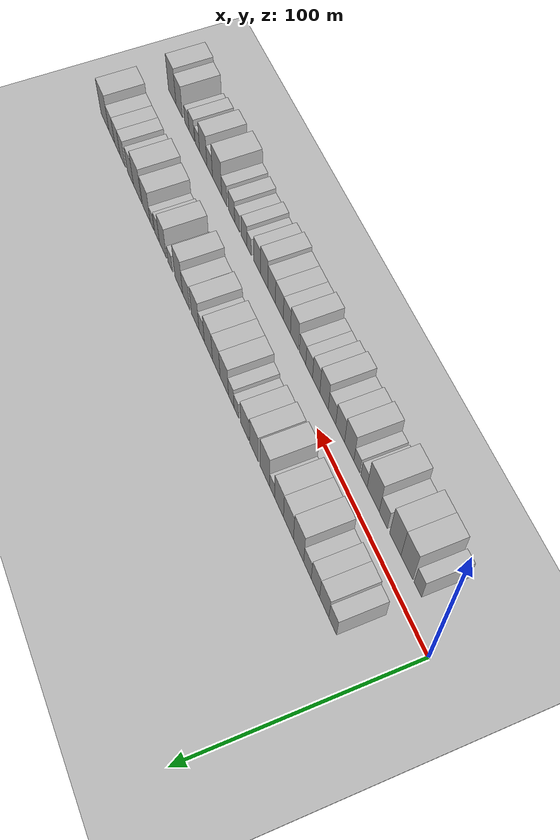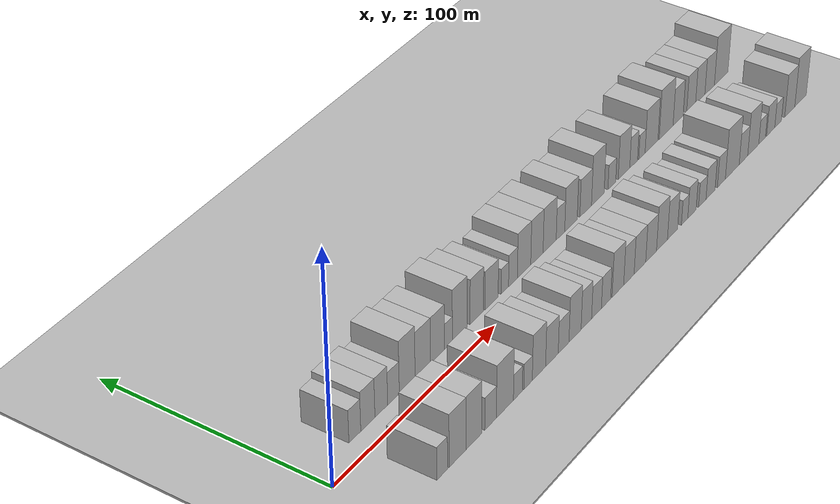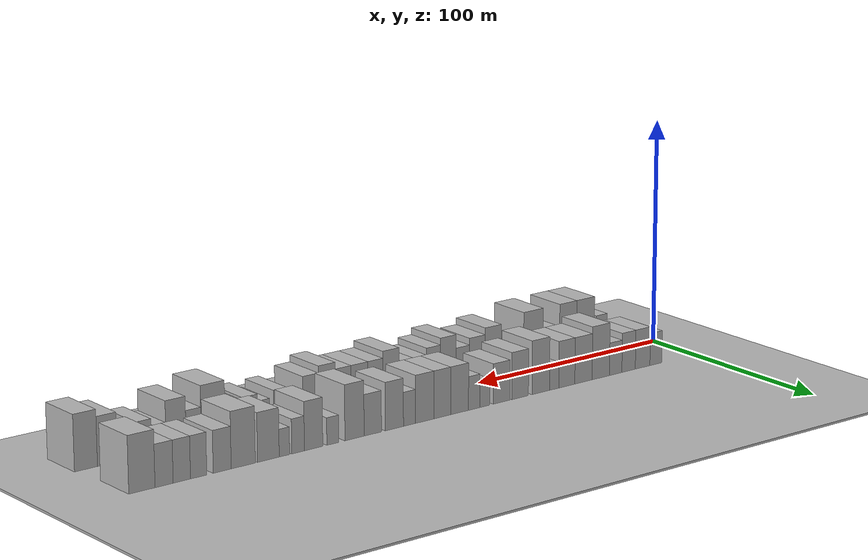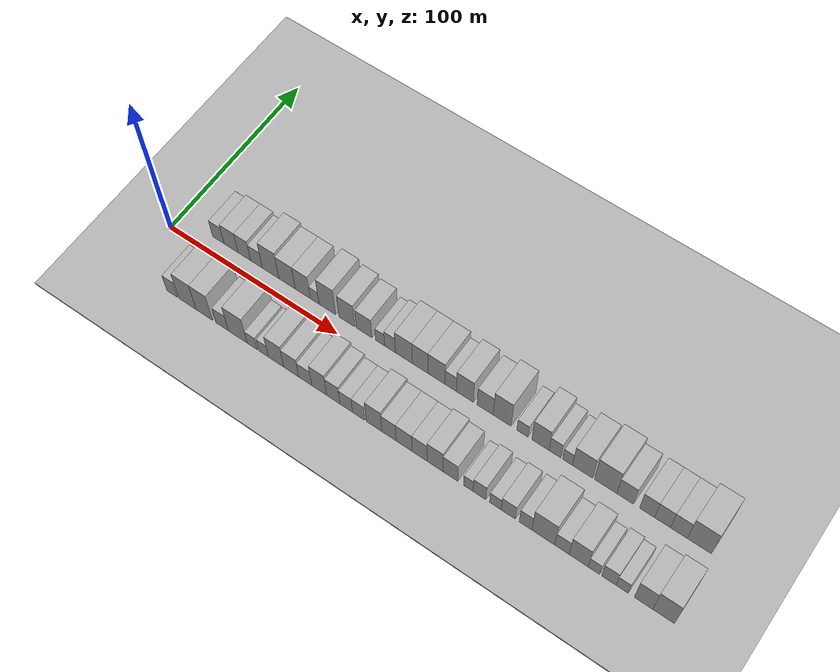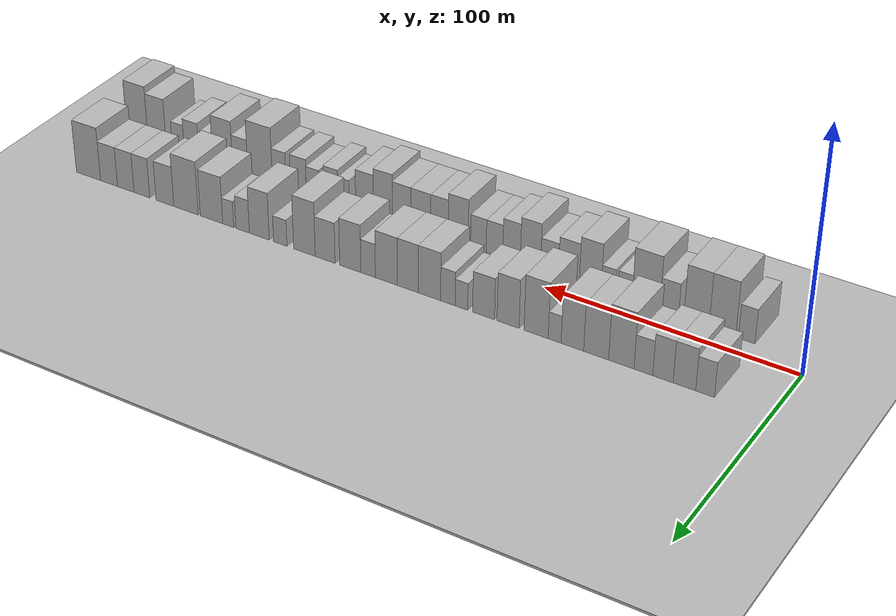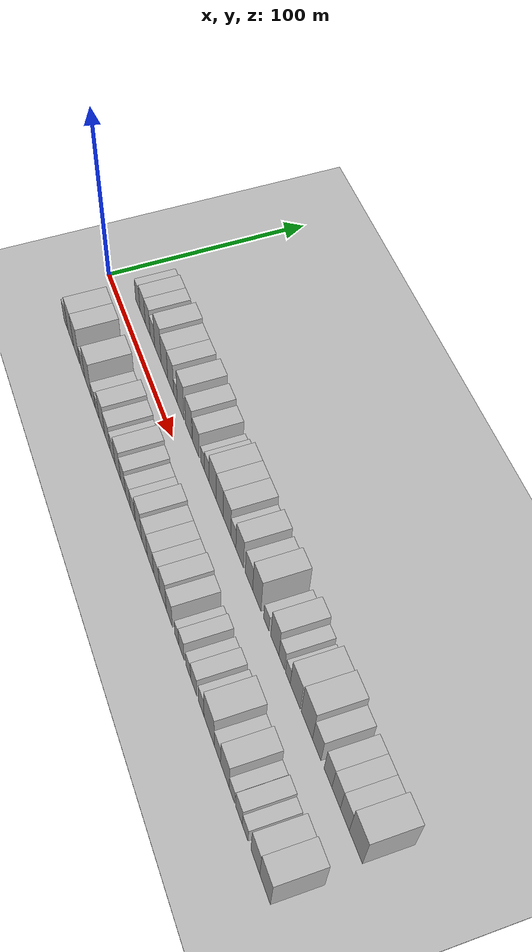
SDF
<?xml version="1.0" encoding="utf-8"?>

<sdf version="1.6">

   <world name="default">

      <gui fullscreen="0">

         <camera name="user_camera">

            <pose>-15 0 4.57585 0 0 0</pose>

            <view_controller>orbit</view_controller>

         </camera>

      </gui>

      <scene>

         <sky>

           <clouds>

             <speed>12</speed>

           </clouds>

         </sky>

         <ambient>0.4 0.4 0.4 1</ambient>

         <background>0.7 0.7 0.7 1</background>

         <shadows>1</shadows>

      </scene>

      <gravity>0 0 -9.8066</gravity>

      <magnetic_field>6e-06 2.3e-05 -4.2e-05</magnetic_field>

      <physics default="0" name="default_physics" type="ode">

         <ode>

            <solver>

               <type>quick</type>

               <iters>10</iters>

               <sor>1.0</sor>

               <use_dynamic_moi_rescaling>0</use_dynamic_moi_rescaling>

            </solver>

            <constraints>

               <cfm>0</cfm>

               <erp>0.2</erp>

               <contact_max_correcting_vel>100</contact_max_correcting_vel>

               <contact_surface_layer>0.001</contact_surface_layer>

            </constraints>

         </ode>

         <max_step_size>0.004</max_step_size>

         <real_time_factor>1</real_time_factor>

         <real_time_update_rate>250</real_time_update_rate>

      </physics>

      <light name="sun" type="directional">

         <cast_shadows>1</cast_shadows>

         <pose>0 0 10 0 0 0</pose>

         <diffuse>0.8 0.8 0.8 1</diffuse>

         <specular>0.2 0.2 0.2 1</specular>

         <attenuation>

            <range>1000</range>

            <constant>0.9</constant>

            <linear>0.01</linear>

            <quadratic>0.001</quadratic>

         </attenuation>

         <direction>-0.5 0.1 -0.9</direction>

      </light>

      <include>

         <name>ground_plane_1</name>

         <uri>model://HANNAS_ground_plane</uri>

         <pose>0 0 0  0 0 0</pose>

      </include>

      <include>

         <name>ground_plane_2</name>

         <uri>model://HANNAS_ground_plane</uri>

         <pose>100 0 0  0 0 0</pose>

      </include>

      <model name="building_1">

         <static>1</static>

         <pose frame="">23.4811 17.5000 0 0.000000 0.000000 1.570796</pose>

         <link name="link">

            <pose frame="">0 0 7.50 0 0 0</pose>

            <collision name="collision">

               <geometry>

                  <box>

                     <size>20.0000 6.9621 15.0000</size>

                  </box>

               </geometry>

               <max_contacts>10</max_contacts>

               <surface>

                  <contact>

                     <ode/>

                  </contact>

                  <bounce/>

                  <friction>

                     <torsional>

                        <ode/>

                     </torsional>

                     <ode/>

                  </friction>

               </surface>

            </collision>

            <visual name="visual">

               <cast_shadows>0</cast_shadows>

               <geometry>

                  <box>

                     <size>20.0000 6.9621 15.0000</size>

                  </box>

               </geometry>

               <material>

                  <script>

                     <uri>model://HANNAS_wall/materials/scripts</uri>

                     <uri>model://HANNAS_wall/materials/textures</uri>

                     <name>vrc/HANNAS_wall</name>

                  </script>

               </material>

            </visual>

            <self_collide>0</self_collide>

            <enable_wind>0</enable_wind>

            <kinematic>0</kinematic>

         </link>

      </model>

      <model name="building_2">

         <static>1</static>

         <pose frame="">31.1771 17.5000 0 0.000000 0.000000 1.570796</pose>

         <link name="link">

            <pose frame="">0 0 9.00 0 0 0</pose>

            <collision name="collision">

               <geometry>

                  <box>

                     <size>20.0000 8.4299 18.0000</size>

                  </box>

               </geometry>

               <max_contacts>10</max_contacts>

               <surface>

                  <contact>

                     <ode/>

                  </contact>

                  <bounce/>

                  <friction>

                     <torsional>

                        <ode/>

                     </torsional>

                     <ode/>

                  </friction>

               </surface>

            </collision>

            <visual name="visual">

               <cast_shadows>0</cast_shadows>

               <geometry>

                  <box>

                     <size>20.0000 8.4299 18.0000</size>

                  </box>

               </geometry>

               <material>

                  <script>

                     <uri>model://HANNAS_wall/materials/scripts</uri>

                     <uri>model://HANNAS_wall/materials/textures</uri>

                     <name>vrc/HANNAS_wall</name>

                  </script>

               </material>

            </visual>

            <self_collide>0</self_collide>

            <enable_wind>0</enable_wind>

            <kinematic>0</kinematic>

         </link>

      </model>

      <model name="building_3">

         <static>1</static>

         <pose frame="">39.2405 17.5000 0 0.000000 0.000000 1.570796</pose>

         <link name="link">

            <pose frame="">0 0 9.00 0 0 0</pose>

            <collision name="collision">

               <geometry>

                  <box>

                     <size>20.0000 7.6969 18.0000</size>

                  </box>

               </geometry>

               <max_contacts>10</max_contacts>

               <surface>

                  <contact>

                     <ode/>

                  </contact>

                  <bounce/>

                  <friction>

                     <torsional>

                        <ode/>

                     </torsional>

                     <ode/>

                  </friction>

               </surface>

            </collision>

            <visual name="visual">

               <cast_shadows>0</cast_shadows>

               <geometry>

                  <box>

                     <size>20.0000 7.6969 18.0000</size>

                  </box>

               </geometry>

               <material>

                  <script>

                     <uri>model://HANNAS_wall/materials/scripts</uri>

                     <uri>model://HANNAS_wall/materials/textures</uri>

                     <name>vrc/HANNAS_wall</name>

                  </script>

               </material>

            </visual>

            <self_collide>0</self_collide>

            <enable_wind>0</enable_wind>

            <kinematic>0</kinematic>

         </link>

      </model>

      <model name="building_4">

         <static>1</static>

         <pose frame="">46.6445 17.5000 0 0.000000 0.000000 1.570796</pose>

         <link name="link">

            <pose frame="">0 0 7.50 0 0 0</pose>

            <collision name="collision">

               <geometry>

                  <box>

                     <size>20.0000 7.1112 15.0000</size>

                  </box>

               </geometry>

               <max_contacts>10</max_contacts>

               <surface>

                  <contact>

                     <ode/>

                  </contact>

                  <bounce/>

                  <friction>

                     <torsional>

                        <ode/>

                     </torsional>

                     <ode/>

                  </friction>

               </surface>

            </collision>

            <visual name="visual">

               <cast_shadows>0</cast_shadows>

               <geometry>

                  <box>

                     <size>20.0000 7.1112 15.0000</size>

                  </box>

               </geometry>

               <material>

                  <script>

                     <uri>model://HANNAS_wall/materials/scripts</uri>

                     <uri>model://HANNAS_wall/materials/textures</uri>

                     <name>vrc/HANNAS_wall</name>

                  </script>

               </material>

            </visual>

            <self_collide>0</self_collide>

            <enable_wind>0</enable_wind>

            <kinematic>0</kinematic>

         </link>

      </model>

      <model name="building_5">

         <static>1</static>

         <pose frame="">55.1013 17.5000 0 0.000000 0.000000 1.570796</pose>

         <link name="link">

            <pose frame="">0 0 12.00 0 0 0</pose>

            <collision name="collision">

               <geometry>

                  <box>

                     <size>20.0000 9.8022 24.0000</size>

                  </box>

               </geometry>

               <max_contacts>10</max_contacts>

               <surface>

                  <contact>

                     <ode/>

                  </contact>

                  <bounce/>

                  <friction>

                     <torsional>

                        <ode/>

                     </torsional>

                     <ode/>

                  </friction>

               </surface>

            </collision>

            <visual name="visual">

               <cast_shadows>0</cast_shadows>

               <geometry>

                  <box>

                     <size>20.0000 9.8022 24.0000</size>

                  </box>

               </geometry>

               <material>

                  <script>

                     <uri>model://HANNAS_wall/materials/scripts</uri>

                     <uri>model://HANNAS_wall/materials/textures</uri>

                     <name>vrc/HANNAS_wall</name>

                  </script>

               </material>

            </visual>

            <self_collide>0</self_collide>

            <enable_wind>0</enable_wind>

            <kinematic>0</kinematic>

         </link>

      </model>

      <model name="building_6">

         <static>1</static>

         <pose frame="">64.8495 17.5000 0 0.000000 0.000000 1.570796</pose>

         <link name="link">

            <pose frame="">0 0 10.50 0 0 0</pose>

            <collision name="collision">

               <geometry>

                  <box>

                     <size>20.0000 9.6944 21.0000</size>

                  </box>

               </geometry>

               <max_contacts>10</max_contacts>

               <surface>

                  <contact>

                     <ode/>

                  </contact>

                  <bounce/>

                  <friction>

                     <torsional>

                        <ode/>

                     </torsional>

                     <ode/>

                  </friction>

               </surface>

            </collision>

            <visual name="visual">

               <cast_shadows>0</cast_shadows>

               <geometry>

                  <box>

                     <size>20.0000 9.6944 21.0000</size>

                  </box>

               </geometry>

               <material>

                  <script>

                     <uri>model://HANNAS_wall/materials/scripts</uri>

                     <uri>model://HANNAS_wall/materials/textures</uri>

                     <name>vrc/HANNAS_wall</name>

                  </script>

               </material>

            </visual>

            <self_collide>0</self_collide>

            <enable_wind>0</enable_wind>

            <kinematic>0</kinematic>

         </link>

      </model>

      <model name="building_7">

         <static>1</static>

         <pose frame="">74.1462 17.5000 0 0.000000 0.000000 1.570796</pose>

         <link name="link">

            <pose frame="">0 0 10.50 0 0 0</pose>

            <collision name="collision">

               <geometry>

                  <box>

                     <size>20.0000 8.8989 21.0000</size>

                  </box>

               </geometry>

               <max_contacts>10</max_contacts>

               <surface>

                  <contact>

                     <ode/>

                  </contact>

                  <bounce/>

                  <friction>

                     <torsional>

                        <ode/>

                     </torsional>

                     <ode/>

                  </friction>

               </surface>

            </collision>

            <visual name="visual">

               <cast_shadows>0</cast_shadows>

               <geometry>

                  <box>

                     <size>20.0000 8.8989 21.0000</size>

                  </box>

               </geometry>

               <material>

                  <script>

                     <uri>model://HANNAS_wall/materials/scripts</uri>

                     <uri>model://HANNAS_wall/materials/textures</uri>

                     <name>vrc/HANNAS_wall</name>

                  </script>

               </material>

            </visual>

            <self_collide>0</self_collide>

            <enable_wind>0</enable_wind>

            <kinematic>0</kinematic>

         </link>

      </model>

      <model name="building_8">

         <static>1</static>

         <pose frame="">81.1562 17.5000 0 0.000000 0.000000 1.570796</pose>

         <link name="link">

            <pose frame="">0 0 6.00 0 0 0</pose>

            <collision name="collision">

               <geometry>

                  <box>

                     <size>20.0000 5.1211 12.0000</size>

                  </box>

               </geometry>

               <max_contacts>10</max_contacts>

               <surface>

                  <contact>

                     <ode/>

                  </contact>

                  <bounce/>

                  <friction>

                     <torsional>

                        <ode/>

                     </torsional>

                     <ode/>

                  </friction>

               </surface>

            </collision>

            <visual name="visual">

               <cast_shadows>0</cast_shadows>

               <geometry>

                  <box>

                     <size>20.0000 5.1211 12.0000</size>

                  </box>

               </geometry>

               <material>

                  <script>

                     <uri>model://HANNAS_wall/materials/scripts</uri>

                     <uri>model://HANNAS_wall/materials/textures</uri>

                     <name>vrc/HANNAS_wall</name>

                  </script>

               </material>

            </visual>

            <self_collide>0</self_collide>

            <enable_wind>0</enable_wind>

            <kinematic>0</kinematic>

         </link>

      </model>

      <model name="building_9">

         <static>1</static>

         <pose frame="">88.5220 17.5000 0 0.000000 0.000000 1.570796</pose>

         <link name="link">

            <pose frame="">0 0 12.00 0 0 0</pose>

            <collision name="collision">

               <geometry>

                  <box>

                     <size>20.0000 9.6105 24.0000</size>

                  </box>

               </geometry>

               <max_contacts>10</max_contacts>

               <surface>

                  <contact>

                     <ode/>

                  </contact>

                  <bounce/>

                  <friction>

                     <torsional>

                        <ode/>

                     </torsional>

                     <ode/>

                  </friction>

               </surface>

            </collision>

            <visual name="visual">

               <cast_shadows>0</cast_shadows>

               <geometry>

                  <box>

                     <size>20.0000 9.6105 24.0000</size>

                  </box>

               </geometry>

               <material>

                  <script>

                     <uri>model://HANNAS_wall/materials/scripts</uri>

                     <uri>model://HANNAS_wall/materials/textures</uri>

                     <name>vrc/HANNAS_wall</name>

                  </script>

               </material>

            </visual>

            <self_collide>0</self_collide>

            <enable_wind>0</enable_wind>

            <kinematic>0</kinematic>

         </link>

      </model>

      <model name="building_10">

         <static>1</static>

         <pose frame="">99.8044 17.5000 0 0.000000 0.000000 1.570796</pose>

         <link name="link">

            <pose frame="">0 0 10.50 0 0 0</pose>

            <collision name="collision">

               <geometry>

                  <box>

                     <size>20.0000 8.9543 21.0000</size>

                  </box>

               </geometry>

               <max_contacts>10</max_contacts>

               <surface>

                  <contact>

                     <ode/>

                  </contact>

                  <bounce/>

                  <friction>

                     <torsional>

                        <ode/>

                     </torsional>

                     <ode/>

                  </friction>

               </surface>

            </collision>

            <visual name="visual">

               <cast_shadows>0</cast_shadows>

               <geometry>

                  <box>

                     <size>20.0000 8.9543 21.0000</size>

                  </box>

               </geometry>

               <material>

                  <script>

                     <uri>model://HANNAS_wall/materials/scripts</uri>

                     <uri>model://HANNAS_wall/materials/textures</uri>

                     <name>vrc/HANNAS_wall</name>

                  </script>

               </material>

            </visual>

            <self_collide>0</self_collide>

            <enable_wind>0</enable_wind>

            <kinematic>0</kinematic>

         </link>

      </model>

      <model name="building_11">

         <static>1</static>

         <pose frame="">109.7610 17.5000 0 0.000000 0.000000 1.570796</pose>

         <link name="link">

            <pose frame="">0 0 9.00 0 0 0</pose>

            <collision name="collision">

               <geometry>

                  <box>

                     <size>20.0000 8.9589 18.0000</size>

                  </box>

               </geometry>

               <max_contacts>10</max_contacts>

               <surface>

                  <contact>

                     <ode/>

                  </contact>

                  <bounce/>

                  <friction>

                     <torsional>

                        <ode/>

                     </torsional>

                     <ode/>

                  </friction>

               </surface>

            </collision>

            <visual name="visual">

               <cast_shadows>0</cast_shadows>

               <geometry>

                  <box>

                     <size>20.0000 8.9589 18.0000</size>

                  </box>

               </geometry>

               <material>

                  <script>

                     <uri>model://HANNAS_wall/materials/scripts</uri>

                     <uri>model://HANNAS_wall/materials/textures</uri>

                     <name>vrc/HANNAS_wall</name>

                  </script>

               </material>

            </visual>

            <self_collide>0</self_collide>

            <enable_wind>0</enable_wind>

            <kinematic>0</kinematic>

         </link>

      </model>

      <model name="building_12">

         <static>1</static>

         <pose frame="">118.8123 17.5000 0 0.000000 0.000000 1.570796</pose>

         <link name="link">

            <pose frame="">0 0 6.00 0 0 0</pose>

            <collision name="collision">

               <geometry>

                  <box>

                     <size>20.0000 5.1439 12.0000</size>

                  </box>

               </geometry>

               <max_contacts>10</max_contacts>

               <surface>

                  <contact>

                     <ode/>

                  </contact>

                  <bounce/>

                  <friction>

                     <torsional>

                        <ode/>

                     </torsional>

                     <ode/>

                  </friction>

               </surface>

            </collision>

            <visual name="visual">

               <cast_shadows>0</cast_shadows>

               <geometry>

                  <box>

                     <size>20.0000 5.1439 12.0000</size>

                  </box>

               </geometry>

               <material>

                  <script>

                     <uri>model://HANNAS_wall/materials/scripts</uri>

                     <uri>model://HANNAS_wall/materials/textures</uri>

                     <name>vrc/HANNAS_wall</name>

                  </script>

               </material>

            </visual>

            <self_collide>0</self_collide>

            <enable_wind>0</enable_wind>

            <kinematic>0</kinematic>

         </link>

      </model>

      <model name="building_13">

         <static>1</static>

         <pose frame="">124.4371 17.5000 0 0.000000 0.000000 1.570796</pose>

         <link name="link">

            <pose frame="">0 0 7.50 0 0 0</pose>

            <collision name="collision">

               <geometry>

                  <box>

                     <size>20.0000 6.1056 15.0000</size>

                  </box>

               </geometry>

               <max_contacts>10</max_contacts>

               <surface>

                  <contact>

                     <ode/>

                  </contact>

                  <bounce/>

                  <friction>

                     <torsional>

                        <ode/>

                     </torsional>

                     <ode/>

                  </friction>

               </surface>

            </collision>

            <visual name="visual">

               <cast_shadows>0</cast_shadows>

               <geometry>

                  <box>

                     <size>20.0000 6.1056 15.0000</size>

                  </box>

               </geometry>

               <material>

                  <script>

                     <uri>model://HANNAS_wall/materials/scripts</uri>

                     <uri>model://HANNAS_wall/materials/textures</uri>

                     <name>vrc/HANNAS_wall</name>

                  </script>

               </material>

            </visual>

            <self_collide>0</self_collide>

            <enable_wind>0</enable_wind>

            <kinematic>0</kinematic>

         </link>

      </model>

      <model name="building_14">

         <static>1</static>

         <pose frame="">132.1952 17.5000 0 0.000000 0.000000 1.570796</pose>

         <link name="link">

            <pose frame="">0 0 10.50 0 0 0</pose>

            <collision name="collision">

               <geometry>

                  <box>

                     <size>20.0000 9.4107 21.0000</size>

                  </box>

               </geometry>

               <max_contacts>10</max_contacts>

               <surface>

                  <contact>

                     <ode/>

                  </contact>

                  <bounce/>

                  <friction>

                     <torsional>

                        <ode/>

                     </torsional>

                     <ode/>

                  </friction>

               </surface>

            </collision>

            <visual name="visual">

               <cast_shadows>0</cast_shadows>

               <geometry>

                  <box>

                     <size>20.0000 9.4107 21.0000</size>

                  </box>

               </geometry>

               <material>

                  <script>

                     <uri>model://HANNAS_wall/materials/scripts</uri>

                     <uri>model://HANNAS_wall/materials/textures</uri>

                     <name>vrc/HANNAS_wall</name>

                  </script>

               </material>

            </visual>

            <self_collide>0</self_collide>

            <enable_wind>0</enable_wind>

            <kinematic>0</kinematic>

         </link>

      </model>

      <model name="building_15">

         <static>1</static>

         <pose frame="">141.2868 17.5000 0 0.000000 0.000000 1.570796</pose>

         <link name="link">

            <pose frame="">0 0 10.50 0 0 0</pose>

            <collision name="collision">

               <geometry>

                  <box>

                     <size>20.0000 8.7725 21.0000</size>

                  </box>

               </geometry>

               <max_contacts>10</max_contacts>

               <surface>

                  <contact>

                     <ode/>

                  </contact>

                  <bounce/>

                  <friction>

                     <torsional>

                        <ode/>

                     </torsional>

                     <ode/>

                  </friction>

               </surface>

            </collision>

            <visual name="visual">

               <cast_shadows>0</cast_shadows>

               <geometry>

                  <box>

                     <size>20.0000 8.7725 21.0000</size>

                  </box>

               </geometry>

               <material>

                  <script>

                     <uri>model://HANNAS_wall/materials/scripts</uri>

                     <uri>model://HANNAS_wall/materials/textures</uri>

                     <name>vrc/HANNAS_wall</name>

                  </script>

               </material>

            </visual>

            <self_collide>0</self_collide>

            <enable_wind>0</enable_wind>

            <kinematic>0</kinematic>

         </link>

      </model>

      <model name="building_16">

         <static>1</static>

         <pose frame="">150.4094 17.5000 0 0.000000 0.000000 1.570796</pose>

         <link name="link">

            <pose frame="">0 0 10.50 0 0 0</pose>

            <collision name="collision">

               <geometry>

                  <box>

                     <size>20.0000 9.4727 21.0000</size>

                  </box>

               </geometry>

               <max_contacts>10</max_contacts>

               <surface>

                  <contact>

                     <ode/>

                  </contact>

                  <bounce/>

                  <friction>

                     <torsional>

                        <ode/>

                     </torsional>

                     <ode/>

                  </friction>

               </surface>

            </collision>

            <visual name="visual">

               <cast_shadows>0</cast_shadows>

               <geometry>

                  <box>

                     <size>20.0000 9.4727 21.0000</size>

                  </box>

               </geometry>

               <material>

                  <script>

                     <uri>model://HANNAS_wall/materials/scripts</uri>

                     <uri>model://HANNAS_wall/materials/textures</uri>

                     <name>vrc/HANNAS_wall</name>

                  </script>

               </material>

            </visual>

            <self_collide>0</self_collide>

            <enable_wind>0</enable_wind>

            <kinematic>0</kinematic>

         </link>

      </model>

      <model name="building_17">

         <static>1</static>

         <pose frame="">158.2649 17.5000 0 0.000000 0.000000 1.570796</pose>

         <link name="link">

            <pose frame="">0 0 7.50 0 0 0</pose>

            <collision name="collision">

               <geometry>

                  <box>

                     <size>20.0000 6.2384 15.0000</size>

                  </box>

               </geometry>

               <max_contacts>10</max_contacts>

               <surface>

                  <contact>

                     <ode/>

                  </contact>

                  <bounce/>

                  <friction>

                     <torsional>

                        <ode/>

                     </torsional>

                     <ode/>

                  </friction>

               </surface>

            </collision>

            <visual name="visual">

               <cast_shadows>0</cast_shadows>

               <geometry>

                  <box>

                     <size>20.0000 6.2384 15.0000</size>

                  </box>

               </geometry>

               <material>

                  <script>

                     <uri>model://HANNAS_wall/materials/scripts</uri>

                     <uri>model://HANNAS_wall/materials/textures</uri>

                     <name>vrc/HANNAS_wall</name>

                  </script>

               </material>

            </visual>

            <self_collide>0</self_collide>

            <enable_wind>0</enable_wind>

            <kinematic>0</kinematic>

         </link>

      </model>

      <model name="building_18">

         <static>1</static>

         <pose frame="">166.0009 17.5000 0 0.000000 0.000000 1.570796</pose>

         <link name="link">

            <pose frame="">0 0 10.50 0 0 0</pose>

            <collision name="collision">

               <geometry>

                  <box>

                     <size>20.0000 9.2335 21.0000</size>

                  </box>

               </geometry>

               <max_contacts>10</max_contacts>

               <surface>

                  <contact>

                     <ode/>

                  </contact>

                  <bounce/>

                  <friction>

                     <torsional>

                        <ode/>

                     </torsional>

                     <ode/>

                  </friction>

               </surface>

            </collision>

            <visual name="visual">

               <cast_shadows>0</cast_shadows>

               <geometry>

                  <box>

                     <size>20.0000 9.2335 21.0000</size>

                  </box>

               </geometry>

               <material>

                  <script>

                     <uri>model://HANNAS_wall/materials/scripts</uri>

                     <uri>model://HANNAS_wall/materials/textures</uri>

                     <name>vrc/HANNAS_wall</name>

                  </script>

               </material>

            </visual>

            <self_collide>0</self_collide>

            <enable_wind>0</enable_wind>

            <kinematic>0</kinematic>

         </link>

      </model>

      <model name="building_19">

         <static>1</static>

         <pose frame="">176.9947 17.5000 0 0.000000 0.000000 1.570796</pose>

         <link name="link">

            <pose frame="">0 0 9.00 0 0 0</pose>

            <collision name="collision">

               <geometry>

                  <box>

                     <size>20.0000 8.7541 18.0000</size>

                  </box>

               </geometry>

               <max_contacts>10</max_contacts>

               <surface>

                  <contact>

                     <ode/>

                  </contact>

                  <bounce/>

                  <friction>

                     <torsional>

                        <ode/>

                     </torsional>

                     <ode/>

                  </friction>

               </surface>

            </collision>

            <visual name="visual">

               <cast_shadows>0</cast_shadows>

               <geometry>

                  <box>

                     <size>20.0000 8.7541 18.0000</size>

                  </box>

               </geometry>

               <material>

                  <script>

                     <uri>model://HANNAS_wall/materials/scripts</uri>

                     <uri>model://HANNAS_wall/materials/textures</uri>

                     <name>vrc/HANNAS_wall</name>

                  </script>

               </material>

            </visual>

            <self_collide>0</self_collide>

            <enable_wind>0</enable_wind>

            <kinematic>0</kinematic>

         </link>

      </model>

      <model name="building_20">

         <static>1</static>

         <pose frame="">186.1790 17.5000 0 0.000000 0.000000 1.570796</pose>

         <link name="link">

            <pose frame="">0 0 12.00 0 0 0</pose>

            <collision name="collision">

               <geometry>

                  <box>

                     <size>20.0000 9.6145 24.0000</size>

                  </box>

               </geometry>

               <max_contacts>10</max_contacts>

               <surface>

                  <contact>

                     <ode/>

                  </contact>

                  <bounce/>

                  <friction>

                     <torsional>

                        <ode/>

                     </torsional>

                     <ode/>

                  </friction>

               </surface>

            </collision>

            <visual name="visual">

               <cast_shadows>0</cast_shadows>

               <geometry>

                  <box>

                     <size>20.0000 9.6145 24.0000</size>

                  </box>

               </geometry>

               <material>

                  <script>

                     <uri>model://HANNAS_wall/materials/scripts</uri>

                     <uri>model://HANNAS_wall/materials/textures</uri>

                     <name>vrc/HANNAS_wall</name>

                  </script>

               </material>

            </visual>

            <self_collide>0</self_collide>

            <enable_wind>0</enable_wind>

            <kinematic>0</kinematic>

         </link>

      </model>

      <model name="building_21">

         <static>1</static>

         <pose frame="">196.9758 17.5000 0 0.000000 0.000000 1.570796</pose>

         <link name="link">

            <pose frame="">0 0 6.00 0 0 0</pose>

            <collision name="collision">

               <geometry>

                  <box>

                     <size>20.0000 5.9790 12.0000</size>

                  </box>

               </geometry>

               <max_contacts>10</max_contacts>

               <surface>

                  <contact>

                     <ode/>

                  </contact>

                  <bounce/>

                  <friction>

                     <torsional>

                        <ode/>

                     </torsional>

                     <ode/>

                  </friction>

               </surface>

            </collision>

            <visual name="visual">

               <cast_shadows>0</cast_shadows>

               <geometry>

                  <box>

                     <size>20.0000 5.9790 12.0000</size>

                  </box>

               </geometry>

               <material>

                  <script>

                     <uri>model://HANNAS_wall/materials/scripts</uri>

                     <uri>model://HANNAS_wall/materials/textures</uri>

                     <name>vrc/HANNAS_wall</name>

                  </script>

               </material>

            </visual>

            <self_collide>0</self_collide>

            <enable_wind>0</enable_wind>

            <kinematic>0</kinematic>

         </link>

      </model>

      <model name="building_22">

         <static>1</static>

         <pose frame="">206.4749 17.5000 0 0.000000 0.000000 1.570796</pose>

         <link name="link">

            <pose frame="">0 0 10.50 0 0 0</pose>

            <collision name="collision">

               <geometry>

                  <box>

                     <size>20.0000 9.0193 21.0000</size>

                  </box>

               </geometry>

               <max_contacts>10</max_contacts>

               <surface>

                  <contact>

                     <ode/>

                  </contact>

                  <bounce/>

                  <friction>

                     <torsional>

                        <ode/>

                     </torsional>

                     <ode/>

                  </friction>

               </surface>

            </collision>

            <visual name="visual">

               <cast_shadows>0</cast_shadows>

               <geometry>

                  <box>

                     <size>20.0000 9.0193 21.0000</size>

                  </box>

               </geometry>

               <material>

                  <script>

                     <uri>model://HANNAS_wall/materials/scripts</uri>

                     <uri>model://HANNAS_wall/materials/textures</uri>

                     <name>vrc/HANNAS_wall</name>

                  </script>

               </material>

            </visual>

            <self_collide>0</self_collide>

            <enable_wind>0</enable_wind>

            <kinematic>0</kinematic>

         </link>

      </model>

      <model name="building_23">

         <static>1</static>

         <pose frame="">214.0780 17.5000 0 0.000000 0.000000 1.570796</pose>

         <link name="link">

            <pose frame="">0 0 7.50 0 0 0</pose>

            <collision name="collision">

               <geometry>

                  <box>

                     <size>20.0000 6.1869 15.0000</size>

                  </box>

               </geometry>

               <max_contacts>10</max_contacts>

               <surface>

                  <contact>

                     <ode/>

                  </contact>

                  <bounce/>

                  <friction>

                     <torsional>

                        <ode/>

                     </torsional>

                     <ode/>

                  </friction>

               </surface>

            </collision>

            <visual name="visual">

               <cast_shadows>0</cast_shadows>

               <geometry>

                  <box>

                     <size>20.0000 6.1869 15.0000</size>

                  </box>

               </geometry>

               <material>

                  <script>

                     <uri>model://HANNAS_wall/materials/scripts</uri>

                     <uri>model://HANNAS_wall/materials/textures</uri>

                     <name>vrc/HANNAS_wall</name>

                  </script>

               </material>

            </visual>

            <self_collide>0</self_collide>

            <enable_wind>0</enable_wind>

            <kinematic>0</kinematic>

         </link>

      </model>

      <model name="building_24">

         <static>1</static>

         <pose frame="">220.7017 17.5000 0 0.000000 0.000000 1.570796</pose>

         <link name="link">

            <pose frame="">0 0 6.00 0 0 0</pose>

            <collision name="collision">

               <geometry>

                  <box>

                     <size>20.0000 5.0606 12.0000</size>

                  </box>

               </geometry>

               <max_contacts>10</max_contacts>

               <surface>

                  <contact>

                     <ode/>

                  </contact>

                  <bounce/>

                  <friction>

                     <torsional>

                        <ode/>

                     </torsional>

                     <ode/>

                  </friction>

               </surface>

            </collision>

            <visual name="visual">

               <cast_shadows>0</cast_shadows>

               <geometry>

                  <box>

                     <size>20.0000 5.0606 12.0000</size>

                  </box>

               </geometry>

               <material>

                  <script>

                     <uri>model://HANNAS_wall/materials/scripts</uri>

                     <uri>model://HANNAS_wall/materials/textures</uri>

                     <name>vrc/HANNAS_wall</name>

                  </script>

               </material>

            </visual>

            <self_collide>0</self_collide>

            <enable_wind>0</enable_wind>

            <kinematic>0</kinematic>

         </link>

      </model>

      <model name="building_25">

         <static>1</static>

         <pose frame="">228.4509 17.5000 0 0.000000 0.000000 1.570796</pose>

         <link name="link">

            <pose frame="">0 0 10.50 0 0 0</pose>

            <collision name="collision">

               <geometry>

                  <box>

                     <size>20.0000 10.4377 21.0000</size>

                  </box>

               </geometry>

               <max_contacts>10</max_contacts>

               <surface>

                  <contact>

                     <ode/>

                  </contact>

                  <bounce/>

                  <friction>

                     <torsional>

                        <ode/>

                     </torsional>

                     <ode/>

                  </friction>

               </surface>

            </collision>

            <visual name="visual">

               <cast_shadows>0</cast_shadows>

               <geometry>

                  <box>

                     <size>20.0000 10.4377 21.0000</size>

                  </box>

               </geometry>

               <material>

                  <script>

                     <uri>model://HANNAS_wall/materials/scripts</uri>

                     <uri>model://HANNAS_wall/materials/textures</uri>

                     <name>vrc/HANNAS_wall</name>

                  </script>

               </material>

            </visual>

            <self_collide>0</self_collide>

            <enable_wind>0</enable_wind>

            <kinematic>0</kinematic>

         </link>

      </model>

      <model name="building_26">

         <static>1</static>

         <pose frame="">240.4115 17.5000 0 0.000000 0.000000 1.570796</pose>

         <link name="link">

            <pose frame="">0 0 12.00 0 0 0</pose>

            <collision name="collision">

               <geometry>

                  <box>

                     <size>20.0000 11.4836 24.0000</size>

                  </box>

               </geometry>

               <max_contacts>10</max_contacts>

               <surface>

                  <contact>

                     <ode/>

                  </contact>

                  <bounce/>

                  <friction>

                     <torsional>

                        <ode/>

                     </torsional>

                     <ode/>

                  </friction>

               </surface>

            </collision>

            <visual name="visual">

               <cast_shadows>0</cast_shadows>

               <geometry>

                  <box>

                     <size>20.0000 11.4836 24.0000</size>

                  </box>

               </geometry>

               <material>

                  <script>

                     <uri>model://HANNAS_wall/materials/scripts</uri>

                     <uri>model://HANNAS_wall/materials/textures</uri>

                     <name>vrc/HANNAS_wall</name>

                  </script>

               </material>

            </visual>

            <self_collide>0</self_collide>

            <enable_wind>0</enable_wind>

            <kinematic>0</kinematic>

         </link>

      </model>

      <model name="building_27">

         <static>1</static>

         <pose frame="">250.3855 17.5000 0 0.000000 0.000000 1.570796</pose>

         <link name="link">

            <pose frame="">0 0 9.00 0 0 0</pose>

            <collision name="collision">

               <geometry>

                  <box>

                     <size>20.0000 8.4643 18.0000</size>

                  </box>

               </geometry>

               <max_contacts>10</max_contacts>

               <surface>

                  <contact>

                     <ode/>

                  </contact>

                  <bounce/>

                  <friction>

                     <torsional>

                        <ode/>

                     </torsional>

                     <ode/>

                  </friction>

               </surface>

            </collision>

            <visual name="visual">

               <cast_shadows>0</cast_shadows>

               <geometry>

                  <box>

                     <size>20.0000 8.4643 18.0000</size>

                  </box>

               </geometry>

               <material>

                  <script>

                     <uri>model://HANNAS_wall/materials/scripts</uri>

                     <uri>model://HANNAS_wall/materials/textures</uri>

                     <name>vrc/HANNAS_wall</name>

                  </script>

               </material>

            </visual>

            <self_collide>0</self_collide>

            <enable_wind>0</enable_wind>

            <kinematic>0</kinematic>

         </link>

      </model>

      <model name="building_28">

         <static>1</static>

         <pose frame="">261.4049 17.5000 0 0.000000 0.000000 1.570796</pose>

         <link name="link">

            <pose frame="">0 0 9.00 0 0 0</pose>

            <collision name="collision">

               <geometry>

                  <box>

                     <size>20.0000 7.5746 18.0000</size>

                  </box>

               </geometry>

               <max_contacts>10</max_contacts>

               <surface>

                  <contact>

                     <ode/>

                  </contact>

                  <bounce/>

                  <friction>

                     <torsional>

                        <ode/>

                     </torsional>

                     <ode/>

                  </friction>

               </surface>

            </collision>

            <visual name="visual">

               <cast_shadows>0</cast_shadows>

               <geometry>

                  <box>

                     <size>20.0000 7.5746 18.0000</size>

                  </box>

               </geometry>

               <material>

                  <script>

                     <uri>model://HANNAS_wall/materials/scripts</uri>

                     <uri>model://HANNAS_wall/materials/textures</uri>

                     <name>vrc/HANNAS_wall</name>

                  </script>

               </material>

            </visual>

            <self_collide>0</self_collide>

            <enable_wind>0</enable_wind>

            <kinematic>0</kinematic>

         </link>

      </model>

      <model name="building_29">

         <static>1</static>

         <pose frame="">269.1881 17.5000 0 0.000000 0.000000 1.570796</pose>

         <link name="link">

            <pose frame="">0 0 9.00 0 0 0</pose>

            <collision name="collision">

               <geometry>

                  <box>

                     <size>20.0000 7.9917 18.0000</size>

                  </box>

               </geometry>

               <max_contacts>10</max_contacts>

               <surface>

                  <contact>

                     <ode/>

                  </contact>

                  <bounce/>

                  <friction>

                     <torsional>

                        <ode/>

                     </torsional>

                     <ode/>

                  </friction>

               </surface>

            </collision>

            <visual name="visual">

               <cast_shadows>0</cast_shadows>

               <geometry>

                  <box>

                     <size>20.0000 7.9917 18.0000</size>

                  </box>

               </geometry>

               <material>

                  <script>

                     <uri>model://HANNAS_wall/materials/scripts</uri>

                     <uri>model://HANNAS_wall/materials/textures</uri>

                     <name>vrc/HANNAS_wall</name>

                  </script>

               </material>

            </visual>

            <self_collide>0</self_collide>

            <enable_wind>0</enable_wind>

            <kinematic>0</kinematic>

         </link>

      </model>

      <model name="building_30">

         <static>1</static>

         <pose frame="">277.3372 17.5000 0 0.000000 0.000000 1.570796</pose>

         <link name="link">

            <pose frame="">0 0 9.00 0 0 0</pose>

            <collision name="collision">

               <geometry>

                  <box>

                     <size>20.0000 8.3066 18.0000</size>

                  </box>

               </geometry>

               <max_contacts>10</max_contacts>

               <surface>

                  <contact>

                     <ode/>

                  </contact>

                  <bounce/>

                  <friction>

                     <torsional>

                        <ode/>

                     </torsional>

                     <ode/>

                  </friction>

               </surface>

            </collision>

            <visual name="visual">

               <cast_shadows>0</cast_shadows>

               <geometry>

                  <box>

                     <size>20.0000 8.3066 18.0000</size>

                  </box>

               </geometry>

               <material>

                  <script>

                     <uri>model://HANNAS_wall/materials/scripts</uri>

                     <uri>model://HANNAS_wall/materials/textures</uri>

                     <name>vrc/HANNAS_wall</name>

                  </script>

               </material>

            </visual>

            <self_collide>0</self_collide>

            <enable_wind>0</enable_wind>

            <kinematic>0</kinematic>

         </link>

      </model>

      <model name="building_31">

         <static>1</static>

         <pose frame="">287.4470 17.5000 0 0.000000 0.000000 1.570796</pose>

         <link name="link">

            <pose frame="">0 0 12.00 0 0 0</pose>

            <collision name="collision">

               <geometry>

                  <box>

                     <size>20.0000 11.9131 24.0000</size>

                  </box>

               </geometry>

               <max_contacts>10</max_contacts>

               <surface>

                  <contact>

                     <ode/>

                  </contact>

                  <bounce/>

                  <friction>

                     <torsional>

                        <ode/>

                     </torsional>

                     <ode/>

                  </friction>

               </surface>

            </collision>

            <visual name="visual">

               <cast_shadows>0</cast_shadows>

               <geometry>

                  <box>

                     <size>20.0000 11.9131 24.0000</size>

                  </box>

               </geometry>

               <material>

                  <script>

                     <uri>model://HANNAS_wall/materials/scripts</uri>

                     <uri>model://HANNAS_wall/materials/textures</uri>

                     <name>vrc/HANNAS_wall</name>

                  </script>

               </material>

            </visual>

            <self_collide>0</self_collide>

            <enable_wind>0</enable_wind>

            <kinematic>0</kinematic>

         </link>

      </model>

      <model name="building_32">

         <static>1</static>

         <pose frame="">24.1783 -17.5000 0 0.000000 0.000000 1.570796</pose>

         <link name="link">

            <pose frame="">0 0 7.50 0 0 0</pose>

            <collision name="collision">

               <geometry>

                  <box>

                     <size>20.0000 6.3566 15.0000</size>

                  </box>

               </geometry>

               <max_contacts>10</max_contacts>

               <surface>

                  <contact>

                     <ode/>

                  </contact>

                  <bounce/>

                  <friction>

                     <torsional>

                        <ode/>

                     </torsional>

                     <ode/>

                  </friction>

               </surface>

            </collision>

            <visual name="visual">

               <cast_shadows>0</cast_shadows>

               <geometry>

                  <box>

                     <size>20.0000 6.3566 15.0000</size>

                  </box>

               </geometry>

               <material>

                  <script>

                     <uri>model://HANNAS_wall/materials/scripts</uri>

                     <uri>model://HANNAS_wall/materials/textures</uri>

                     <name>vrc/HANNAS_wall</name>

                  </script>

               </material>

            </visual>

            <self_collide>0</self_collide>

            <enable_wind>0</enable_wind>

            <kinematic>0</kinematic>

         </link>

      </model>

      <model name="building_33">

         <static>1</static>

         <pose frame="">33.4788 -17.5000 0 0.000000 0.000000 1.570796</pose>

         <link name="link">

            <pose frame="">0 0 12.00 0 0 0</pose>

            <collision name="collision">

               <geometry>

                  <box>

                     <size>20.0000 10.2443 24.0000</size>

                  </box>

               </geometry>

               <max_contacts>10</max_contacts>

               <surface>

                  <contact>

                     <ode/>

                  </contact>

                  <bounce/>

                  <friction>

                     <torsional>

                        <ode/>

                     </torsional>

                     <ode/>

                  </friction>

               </surface>

            </collision>

            <visual name="visual">

               <cast_shadows>0</cast_shadows>

               <geometry>

                  <box>

                     <size>20.0000 10.2443 24.0000</size>

                  </box>

               </geometry>

               <material>

                  <script>

                     <uri>model://HANNAS_wall/materials/scripts</uri>

                     <uri>model://HANNAS_wall/materials/textures</uri>

                     <name>vrc/HANNAS_wall</name>

                  </script>

               </material>

            </visual>

            <self_collide>0</self_collide>

            <enable_wind>0</enable_wind>

            <kinematic>0</kinematic>

         </link>

      </model>

      <model name="building_34">

         <static>1</static>

         <pose frame="">43.5199 -17.5000 0 0.000000 0.000000 1.570796</pose>

         <link name="link">

            <pose frame="">0 0 12.00 0 0 0</pose>

            <collision name="collision">

               <geometry>

                  <box>

                     <size>20.0000 9.8379 24.0000</size>

                  </box>

               </geometry>

               <max_contacts>10</max_contacts>

               <surface>

                  <contact>

                     <ode/>

                  </contact>

                  <bounce/>

                  <friction>

                     <torsional>

                        <ode/>

                     </torsional>

                     <ode/>

                  </friction>

               </surface>

            </collision>

            <visual name="visual">

               <cast_shadows>0</cast_shadows>

               <geometry>

                  <box>

                     <size>20.0000 9.8379 24.0000</size>

                  </box>

               </geometry>

               <material>

                  <script>

                     <uri>model://HANNAS_wall/materials/scripts</uri>

                     <uri>model://HANNAS_wall/materials/textures</uri>

                     <name>vrc/HANNAS_wall</name>

                  </script>

               </material>

            </visual>

            <self_collide>0</self_collide>

            <enable_wind>0</enable_wind>

            <kinematic>0</kinematic>

         </link>

      </model>

      <model name="building_35">

         <static>1</static>

         <pose frame="">54.1131 -17.5000 0 0.000000 0.000000 1.570796</pose>

         <link name="link">

            <pose frame="">0 0 7.50 0 0 0</pose>

            <collision name="collision">

               <geometry>

                  <box>

                     <size>20.0000 7.3484 15.0000</size>

                  </box>

               </geometry>

               <max_contacts>10</max_contacts>

               <surface>

                  <contact>

                     <ode/>

                  </contact>

                  <bounce/>

                  <friction>

                     <torsional>

                        <ode/>

                     </torsional>

                     <ode/>

                  </friction>

               </surface>

            </collision>

            <visual name="visual">

               <cast_shadows>0</cast_shadows>

               <geometry>

                  <box>

                     <size>20.0000 7.3484 15.0000</size>

                  </box>

               </geometry>

               <material>

                  <script>

                     <uri>model://HANNAS_wall/materials/scripts</uri>

                     <uri>model://HANNAS_wall/materials/textures</uri>

                     <name>vrc/HANNAS_wall</name>

                  </script>

               </material>

            </visual>

            <self_collide>0</self_collide>

            <enable_wind>0</enable_wind>

            <kinematic>0</kinematic>

         </link>

      </model>

      <model name="building_36">

         <static>1</static>

         <pose frame="">63.3023 -17.5000 0 0.000000 0.000000 1.570796</pose>

         <link name="link">

            <pose frame="">0 0 12.00 0 0 0</pose>

            <collision name="collision">

               <geometry>

                  <box>

                     <size>20.0000 11.0301 24.0000</size>

                  </box>

               </geometry>

               <max_contacts>10</max_contacts>

               <surface>

                  <contact>

                     <ode/>

                  </contact>

                  <bounce/>

                  <friction>

                     <torsional>

                        <ode/>

                     </torsional>

                     <ode/>

                  </friction>

               </surface>

            </collision>

            <visual name="visual">

               <cast_shadows>0</cast_shadows>

               <geometry>

                  <box>

                     <size>20.0000 11.0301 24.0000</size>

                  </box>

               </geometry>

               <material>

                  <script>

                     <uri>model://HANNAS_wall/materials/scripts</uri>

                     <uri>model://HANNAS_wall/materials/textures</uri>

                     <name>vrc/HANNAS_wall</name>

                  </script>

               </material>

            </visual>

            <self_collide>0</self_collide>

            <enable_wind>0</enable_wind>

            <kinematic>0</kinematic>

         </link>

      </model>

      <model name="building_37">

         <static>1</static>

         <pose frame="">71.7248 -17.5000 0 0.000000 0.000000 1.570796</pose>

         <link name="link">

            <pose frame="">0 0 6.00 0 0 0</pose>

            <collision name="collision">

               <geometry>

                  <box>

                     <size>20.0000 5.8149 12.0000</size>

                  </box>

               </geometry>

               <max_contacts>10</max_contacts>

               <surface>

                  <contact>

                     <ode/>

                  </contact>

                  <bounce/>

                  <friction>

                     <torsional>

                        <ode/>

                     </torsional>

                     <ode/>

                  </friction>

               </surface>

            </collision>

            <visual name="visual">

               <cast_shadows>0</cast_shadows>

               <geometry>

                  <box>

                     <size>20.0000 5.8149 12.0000</size>

                  </box>

               </geometry>

               <material>

                  <script>

                     <uri>model://HANNAS_wall/materials/scripts</uri>

                     <uri>model://HANNAS_wall/materials/textures</uri>

                     <name>vrc/HANNAS_wall</name>

                  </script>

               </material>

            </visual>

            <self_collide>0</self_collide>

            <enable_wind>0</enable_wind>

            <kinematic>0</kinematic>

         </link>

      </model>

      <model name="building_38">

         <static>1</static>

         <pose frame="">78.4183 -17.5000 0 0.000000 0.000000 1.570796</pose>

         <link name="link">

            <pose frame="">0 0 6.00 0 0 0</pose>

            <collision name="collision">

               <geometry>

                  <box>

                     <size>20.0000 5.5720 12.0000</size>

                  </box>

               </geometry>

               <max_contacts>10</max_contacts>

               <surface>

                  <contact>

                     <ode/>

                  </contact>

                  <bounce/>

                  <friction>

                     <torsional>

                        <ode/>

                     </torsional>

                     <ode/>

                  </friction>

               </surface>

            </collision>

            <visual name="visual">

               <cast_shadows>0</cast_shadows>

               <geometry>

                  <box>

                     <size>20.0000 5.5720 12.0000</size>

                  </box>

               </geometry>

               <material>

                  <script>

                     <uri>model://HANNAS_wall/materials/scripts</uri>

                     <uri>model://HANNAS_wall/materials/textures</uri>

                     <name>vrc/HANNAS_wall</name>

                  </script>

               </material>

            </visual>

            <self_collide>0</self_collide>

            <enable_wind>0</enable_wind>

            <kinematic>0</kinematic>

         </link>

      </model>

      <model name="building_39">

         <static>1</static>

         <pose frame="">85.6665 -17.5000 0 0.000000 0.000000 1.570796</pose>

         <link name="link">

            <pose frame="">0 0 10.50 0 0 0</pose>

            <collision name="collision">

               <geometry>

                  <box>

                     <size>20.0000 8.9244 21.0000</size>

                  </box>

               </geometry>

               <max_contacts>10</max_contacts>

               <surface>

                  <contact>

                     <ode/>

                  </contact>

                  <bounce/>

                  <friction>

                     <torsional>

                        <ode/>

                     </torsional>

                     <ode/>

                  </friction>

               </surface>

            </collision>

            <visual name="visual">

               <cast_shadows>0</cast_shadows>

               <geometry>

                  <box>

                     <size>20.0000 8.9244 21.0000</size>

                  </box>

               </geometry>

               <material>

                  <script>

                     <uri>model://HANNAS_wall/materials/scripts</uri>

                     <uri>model://HANNAS_wall/materials/textures</uri>

                     <name>vrc/HANNAS_wall</name>

                  </script>

               </material>

            </visual>

            <self_collide>0</self_collide>

            <enable_wind>0</enable_wind>

            <kinematic>0</kinematic>

         </link>

      </model>

      <model name="building_40">

         <static>1</static>

         <pose frame="">94.4237 -17.5000 0 0.000000 0.000000 1.570796</pose>

         <link name="link">

            <pose frame="">0 0 9.00 0 0 0</pose>

            <collision name="collision">

               <geometry>

                  <box>

                     <size>20.0000 8.5900 18.0000</size>

                  </box>

               </geometry>

               <max_contacts>10</max_contacts>

               <surface>

                  <contact>

                     <ode/>

                  </contact>

                  <bounce/>

                  <friction>

                     <torsional>

                        <ode/>

                     </torsional>

                     <ode/>

                  </friction>

               </surface>

            </collision>

            <visual name="visual">

               <cast_shadows>0</cast_shadows>

               <geometry>

                  <box>

                     <size>20.0000 8.5900 18.0000</size>

                  </box>

               </geometry>

               <material>

                  <script>

                     <uri>model://HANNAS_wall/materials/scripts</uri>

                     <uri>model://HANNAS_wall/materials/textures</uri>

                     <name>vrc/HANNAS_wall</name>

                  </script>

               </material>

            </visual>

            <self_collide>0</self_collide>

            <enable_wind>0</enable_wind>

            <kinematic>0</kinematic>

         </link>

      </model>

      <model name="building_41">

         <static>1</static>

         <pose frame="">102.4037 -17.5000 0 0.000000 0.000000 1.570796</pose>

         <link name="link">

            <pose frame="">0 0 7.50 0 0 0</pose>

            <collision name="collision">

               <geometry>

                  <box>

                     <size>20.0000 7.3700 15.0000</size>

                  </box>

               </geometry>

               <max_contacts>10</max_contacts>

               <surface>

                  <contact>

                     <ode/>

                  </contact>

                  <bounce/>

                  <friction>

                     <torsional>

                        <ode/>

                     </torsional>

                     <ode/>

                  </friction>

               </surface>

            </collision>

            <visual name="visual">

               <cast_shadows>0</cast_shadows>

               <geometry>

                  <box>

                     <size>20.0000 7.3700 15.0000</size>

                  </box>

               </geometry>

               <material>

                  <script>

                     <uri>model://HANNAS_wall/materials/scripts</uri>

                     <uri>model://HANNAS_wall/materials/textures</uri>

                     <name>vrc/HANNAS_wall</name>

                  </script>

               </material>

            </visual>

            <self_collide>0</self_collide>

            <enable_wind>0</enable_wind>

            <kinematic>0</kinematic>

         </link>

      </model>

      <model name="building_42">

         <static>1</static>

         <pose frame="">110.3237 -17.5000 0 0.000000 0.000000 1.570796</pose>

         <link name="link">

            <pose frame="">0 0 10.50 0 0 0</pose>

            <collision name="collision">

               <geometry>

                  <box>

                     <size>20.0000 8.4701 21.0000</size>

                  </box>

               </geometry>

               <max_contacts>10</max_contacts>

               <surface>

                  <contact>

                     <ode/>

                  </contact>

                  <bounce/>

                  <friction>

                     <torsional>

                        <ode/>

                     </torsional>

                     <ode/>

                  </friction>

               </surface>

            </collision>

            <visual name="visual">

               <cast_shadows>0</cast_shadows>

               <geometry>

                  <box>

                     <size>20.0000 8.4701 21.0000</size>

                  </box>

               </geometry>

               <material>

                  <script>

                     <uri>model://HANNAS_wall/materials/scripts</uri>

                     <uri>model://HANNAS_wall/materials/textures</uri>

                     <name>vrc/HANNAS_wall</name>

                  </script>

               </material>

            </visual>

            <self_collide>0</self_collide>

            <enable_wind>0</enable_wind>

            <kinematic>0</kinematic>

         </link>

      </model>

      <model name="building_43">

         <static>1</static>

         <pose frame="">118.2709 -17.5000 0 0.000000 0.000000 1.570796</pose>

         <link name="link">

            <pose frame="">0 0 9.00 0 0 0</pose>

            <collision name="collision">

               <geometry>

                  <box>

                     <size>20.0000 7.4242 18.0000</size>

                  </box>

               </geometry>

               <max_contacts>10</max_contacts>

               <surface>

                  <contact>

                     <ode/>

                  </contact>

                  <bounce/>

                  <friction>

                     <torsional>

                        <ode/>

                     </torsional>

                     <ode/>

                  </friction>

               </surface>

            </collision>

            <visual name="visual">

               <cast_shadows>0</cast_shadows>

               <geometry>

                  <box>

                     <size>20.0000 7.4242 18.0000</size>

                  </box>

               </geometry>

               <material>

                  <script>

                     <uri>model://HANNAS_wall/materials/scripts</uri>

                     <uri>model://HANNAS_wall/materials/textures</uri>

                     <name>vrc/HANNAS_wall</name>

                  </script>

               </material>

            </visual>

            <self_collide>0</self_collide>

            <enable_wind>0</enable_wind>

            <kinematic>0</kinematic>

         </link>

      </model>

      <model name="building_44">

         <static>1</static>

         <pose frame="">125.4866 -17.5000 0 0.000000 0.000000 1.570796</pose>

         <link name="link">

            <pose frame="">0 0 7.50 0 0 0</pose>

            <collision name="collision">

               <geometry>

                  <box>

                     <size>20.0000 7.0073 15.0000</size>

                  </box>

               </geometry>

               <max_contacts>10</max_contacts>

               <surface>

                  <contact>

                     <ode/>

                  </contact>

                  <bounce/>

                  <friction>

                     <torsional>

                        <ode/>

                     </torsional>

                     <ode/>

                  </friction>

               </surface>

            </collision>

            <visual name="visual">

               <cast_shadows>0</cast_shadows>

               <geometry>

                  <box>

                     <size>20.0000 7.0073 15.0000</size>

                  </box>

               </geometry>

               <material>

                  <script>

                     <uri>model://HANNAS_wall/materials/scripts</uri>

                     <uri>model://HANNAS_wall/materials/textures</uri>

                     <name>vrc/HANNAS_wall</name>

                  </script>

               </material>

            </visual>

            <self_collide>0</self_collide>

            <enable_wind>0</enable_wind>

            <kinematic>0</kinematic>

         </link>

      </model>

      <model name="building_45">

         <static>1</static>

         <pose frame="">132.3429 -17.5000 0 0.000000 0.000000 1.570796</pose>

         <link name="link">

            <pose frame="">0 0 7.50 0 0 0</pose>

            <collision name="collision">

               <geometry>

                  <box>

                     <size>20.0000 6.7054 15.0000</size>

                  </box>

               </geometry>

               <max_contacts>10</max_contacts>

               <surface>

                  <contact>

                     <ode/>

                  </contact>

                  <bounce/>

                  <friction>

                     <torsional>

                        <ode/>

                     </torsional>

                     <ode/>

                  </friction>

               </surface>

            </collision>

            <visual name="visual">

               <cast_shadows>0</cast_shadows>

               <geometry>

                  <box>

                     <size>20.0000 6.7054 15.0000</size>

                  </box>

               </geometry>

               <material>

                  <script>

                     <uri>model://HANNAS_wall/materials/scripts</uri>

                     <uri>model://HANNAS_wall/materials/textures</uri>

                     <name>vrc/HANNAS_wall</name>

                  </script>

               </material>

            </visual>

            <self_collide>0</self_collide>

            <enable_wind>0</enable_wind>

            <kinematic>0</kinematic>

         </link>

      </model>

      <model name="building_46">

         <static>1</static>

         <pose frame="">140.9544 -17.5000 0 0.000000 0.000000 1.570796</pose>

         <link name="link">

            <pose frame="">0 0 10.50 0 0 0</pose>

            <collision name="collision">

               <geometry>

                  <box>

                     <size>20.0000 8.5175 21.0000</size>

                  </box>

               </geometry>

               <max_contacts>10</max_contacts>

               <surface>

                  <contact>

                     <ode/>

                  </contact>

                  <bounce/>

                  <friction>

                     <torsional>

                        <ode/>

                     </torsional>

                     <ode/>

                  </friction>

               </surface>

            </collision>

            <visual name="visual">

               <cast_shadows>0</cast_shadows>

               <geometry>

                  <box>

                     <size>20.0000 8.5175 21.0000</size>

                  </box>

               </geometry>

               <material>

                  <script>

                     <uri>model://HANNAS_wall/materials/scripts</uri>

                     <uri>model://HANNAS_wall/materials/textures</uri>

                     <name>vrc/HANNAS_wall</name>

                  </script>

               </material>

            </visual>

            <self_collide>0</self_collide>

            <enable_wind>0</enable_wind>

            <kinematic>0</kinematic>

         </link>

      </model>

      <model name="building_47">

         <static>1</static>

         <pose frame="">149.0824 -17.5000 0 0.000000 0.000000 1.570796</pose>

         <link name="link">

            <pose frame="">0 0 9.00 0 0 0</pose>

            <collision name="collision">

               <geometry>

                  <box>

                     <size>20.0000 7.7385 18.0000</size>

                  </box>

               </geometry>

               <max_contacts>10</max_contacts>

               <surface>

                  <contact>

                     <ode/>

                  </contact>

                  <bounce/>

                  <friction>

                     <torsional>

                        <ode/>

                     </torsional>

                     <ode/>

                  </friction>

               </surface>

            </collision>

            <visual name="visual">

               <cast_shadows>0</cast_shadows>

               <geometry>

                  <box>

                     <size>20.0000 7.7385 18.0000</size>

                  </box>

               </geometry>

               <material>

                  <script>

                     <uri>model://HANNAS_wall/materials/scripts</uri>

                     <uri>model://HANNAS_wall/materials/textures</uri>

                     <name>vrc/HANNAS_wall</name>

                  </script>

               </material>

            </visual>

            <self_collide>0</self_collide>

            <enable_wind>0</enable_wind>

            <kinematic>0</kinematic>

         </link>

      </model>

      <model name="building_48">

         <static>1</static>

         <pose frame="">157.3040 -17.5000 0 0.000000 0.000000 1.570796</pose>

         <link name="link">

            <pose frame="">0 0 9.00 0 0 0</pose>

            <collision name="collision">

               <geometry>

                  <box>

                     <size>20.0000 8.7045 18.0000</size>

                  </box>

               </geometry>

               <max_contacts>10</max_contacts>

               <surface>

                  <contact>

                     <ode/>

                  </contact>

                  <bounce/>

                  <friction>

                     <torsional>

                        <ode/>

                     </torsional>

                     <ode/>

                  </friction>

               </surface>

            </collision>

            <visual name="visual">

               <cast_shadows>0</cast_shadows>

               <geometry>

                  <box>

                     <size>20.0000 8.7045 18.0000</size>

                  </box>

               </geometry>

               <material>

                  <script>

                     <uri>model://HANNAS_wall/materials/scripts</uri>

                     <uri>model://HANNAS_wall/materials/textures</uri>

                     <name>vrc/HANNAS_wall</name>

                  </script>

               </material>

            </visual>

            <self_collide>0</self_collide>

            <enable_wind>0</enable_wind>

            <kinematic>0</kinematic>

         </link>

      </model>

      <model name="building_49">

         <static>1</static>

         <pose frame="">165.7661 -17.5000 0 0.000000 0.000000 1.570796</pose>

         <link name="link">

            <pose frame="">0 0 9.00 0 0 0</pose>

            <collision name="collision">

               <geometry>

                  <box>

                     <size>20.0000 8.2197 18.0000</size>

                  </box>

               </geometry>

               <max_contacts>10</max_contacts>

               <surface>

                  <contact>

                     <ode/>

                  </contact>

                  <bounce/>

                  <friction>

                     <torsional>

                        <ode/>

                     </torsional>

                     <ode/>

                  </friction>

               </surface>

            </collision>

            <visual name="visual">

               <cast_shadows>0</cast_shadows>

               <geometry>

                  <box>

                     <size>20.0000 8.2197 18.0000</size>

                  </box>

               </geometry>

               <material>

                  <script>

                     <uri>model://HANNAS_wall/materials/scripts</uri>

                     <uri>model://HANNAS_wall/materials/textures</uri>

                     <name>vrc/HANNAS_wall</name>

                  </script>

               </material>

            </visual>

            <self_collide>0</self_collide>

            <enable_wind>0</enable_wind>

            <kinematic>0</kinematic>

         </link>

      </model>

      <model name="building_50">

         <static>1</static>

         <pose frame="">174.1009 -17.5000 0 0.000000 0.000000 1.570796</pose>

         <link name="link">

            <pose frame="">0 0 10.50 0 0 0</pose>

            <collision name="collision">

               <geometry>

                  <box>

                     <size>20.0000 8.4498 21.0000</size>

                  </box>

               </geometry>

               <max_contacts>10</max_contacts>

               <surface>

                  <contact>

                     <ode/>

                  </contact>

                  <bounce/>

                  <friction>

                     <torsional>

                        <ode/>

                     </torsional>

                     <ode/>

                  </friction>

               </surface>

            </collision>

            <visual name="visual">

               <cast_shadows>0</cast_shadows>

               <geometry>

                  <box>

                     <size>20.0000 8.4498 21.0000</size>

                  </box>

               </geometry>

               <material>

                  <script>

                     <uri>model://HANNAS_wall/materials/scripts</uri>

                     <uri>model://HANNAS_wall/materials/textures</uri>

                     <name>vrc/HANNAS_wall</name>

                  </script>

               </material>

            </visual>

            <self_collide>0</self_collide>

            <enable_wind>0</enable_wind>

            <kinematic>0</kinematic>

         </link>

      </model>

      <model name="building_51">

         <static>1</static>

         <pose frame="">182.2925 -17.5000 0 0.000000 0.000000 1.570796</pose>

         <link name="link">

            <pose frame="">0 0 9.00 0 0 0</pose>

            <collision name="collision">

               <geometry>

                  <box>

                     <size>20.0000 7.9334 18.0000</size>

                  </box>

               </geometry>

               <max_contacts>10</max_contacts>

               <surface>

                  <contact>

                     <ode/>

                  </contact>

                  <bounce/>

                  <friction>

                     <torsional>

                        <ode/>

                     </torsional>

                     <ode/>

                  </friction>

               </surface>

            </collision>

            <visual name="visual">

               <cast_shadows>0</cast_shadows>

               <geometry>

                  <box>

                     <size>20.0000 7.9334 18.0000</size>

                  </box>

               </geometry>

               <material>

                  <script>

                     <uri>model://HANNAS_wall/materials/scripts</uri>

                     <uri>model://HANNAS_wall/materials/textures</uri>

                     <name>vrc/HANNAS_wall</name>

                  </script>

               </material>

            </visual>

            <self_collide>0</self_collide>

            <enable_wind>0</enable_wind>

            <kinematic>0</kinematic>

         </link>

      </model>

      <model name="building_52">

         <static>1</static>

         <pose frame="">191.7705 -17.5000 0 0.000000 0.000000 1.570796</pose>

         <link name="link">

            <pose frame="">0 0 6.00 0 0 0</pose>

            <collision name="collision">

               <geometry>

                  <box>

                     <size>20.0000 5.0225 12.0000</size>

                  </box>

               </geometry>

               <max_contacts>10</max_contacts>

               <surface>

                  <contact>

                     <ode/>

                  </contact>

                  <bounce/>

                  <friction>

                     <torsional>

                        <ode/>

                     </torsional>

                     <ode/>

                  </friction>

               </surface>

            </collision>

            <visual name="visual">

               <cast_shadows>0</cast_shadows>

               <geometry>

                  <box>

                     <size>20.0000 5.0225 12.0000</size>

                  </box>

               </geometry>

               <material>

                  <script>

                     <uri>model://HANNAS_wall/materials/scripts</uri>

                     <uri>model://HANNAS_wall/materials/textures</uri>

                     <name>vrc/HANNAS_wall</name>

                  </script>

               </material>

            </visual>

            <self_collide>0</self_collide>

            <enable_wind>0</enable_wind>

            <kinematic>0</kinematic>

         </link>

      </model>

      <model name="building_53">

         <static>1</static>

         <pose frame="">197.6247 -17.5000 0 0.000000 0.000000 1.570796</pose>

         <link name="link">

            <pose frame="">0 0 7.50 0 0 0</pose>

            <collision name="collision">

               <geometry>

                  <box>

                     <size>20.0000 6.6860 15.0000</size>

                  </box>

               </geometry>

               <max_contacts>10</max_contacts>

               <surface>

                  <contact>

                     <ode/>

                  </contact>

                  <bounce/>

                  <friction>

                     <torsional>

                        <ode/>

                     </torsional>

                     <ode/>

                  </friction>

               </surface>

            </collision>

            <visual name="visual">

               <cast_shadows>0</cast_shadows>

               <geometry>

                  <box>

                     <size>20.0000 6.6860 15.0000</size>

                  </box>

               </geometry>

               <material>

                  <script>

                     <uri>model://HANNAS_wall/materials/scripts</uri>

                     <uri>model://HANNAS_wall/materials/textures</uri>

                     <name>vrc/HANNAS_wall</name>

                  </script>

               </material>

            </visual>

            <self_collide>0</self_collide>

            <enable_wind>0</enable_wind>

            <kinematic>0</kinematic>

         </link>

      </model>

      <model name="building_54">

         <static>1</static>

         <pose frame="">205.9553 -17.5000 0 0.000000 0.000000 1.570796</pose>

         <link name="link">

            <pose frame="">0 0 6.00 0 0 0</pose>

            <collision name="collision">

               <geometry>

                  <box>

                     <size>20.0000 5.9751 12.0000</size>

                  </box>

               </geometry>

               <max_contacts>10</max_contacts>

               <surface>

                  <contact>

                     <ode/>

                  </contact>

                  <bounce/>

                  <friction>

                     <torsional>

                        <ode/>

                     </torsional>

                     <ode/>

                  </friction>

               </surface>

            </collision>

            <visual name="visual">

               <cast_shadows>0</cast_shadows>

               <geometry>

                  <box>

                     <size>20.0000 5.9751 12.0000</size>

                  </box>

               </geometry>

               <material>

                  <script>

                     <uri>model://HANNAS_wall/materials/scripts</uri>

                     <uri>model://HANNAS_wall/materials/textures</uri>

                     <name>vrc/HANNAS_wall</name>

                  </script>

               </material>

            </visual>

            <self_collide>0</self_collide>

            <enable_wind>0</enable_wind>

            <kinematic>0</kinematic>

         </link>

      </model>

      <model name="building_55">

         <static>1</static>

         <pose frame="">212.6326 -17.5000 0 0.000000 0.000000 1.570796</pose>

         <link name="link">

            <pose frame="">0 0 7.50 0 0 0</pose>

            <collision name="collision">

               <geometry>

                  <box>

                     <size>20.0000 7.3793 15.0000</size>

                  </box>

               </geometry>

               <max_contacts>10</max_contacts>

               <surface>

                  <contact>

                     <ode/>

                  </contact>

                  <bounce/>

                  <friction>

                     <torsional>

                        <ode/>

                     </torsional>

                     <ode/>

                  </friction>

               </surface>

            </collision>

            <visual name="visual">

               <cast_shadows>0</cast_shadows>

               <geometry>

                  <box>

                     <size>20.0000 7.3793 15.0000</size>

                  </box>

               </geometry>

               <material>

                  <script>

                     <uri>model://HANNAS_wall/materials/scripts</uri>

                     <uri>model://HANNAS_wall/materials/textures</uri>

                     <name>vrc/HANNAS_wall</name>

                  </script>

               </material>

            </visual>

            <self_collide>0</self_collide>

            <enable_wind>0</enable_wind>

            <kinematic>0</kinematic>

         </link>

      </model>

      <model name="building_56">

         <static>1</static>

         <pose frame="">221.5893 -17.5000 0 0.000000 0.000000 1.570796</pose>

         <link name="link">

            <pose frame="">0 0 7.50 0 0 0</pose>

            <collision name="collision">

               <geometry>

                  <box>

                     <size>20.0000 6.5341 15.0000</size>

                  </box>

               </geometry>

               <max_contacts>10</max_contacts>

               <surface>

                  <contact>

                     <ode/>

                  </contact>

                  <bounce/>

                  <friction>

                     <torsional>

                        <ode/>

                     </torsional>

                     <ode/>

                  </friction>

               </surface>

            </collision>

            <visual name="visual">

               <cast_shadows>0</cast_shadows>

               <geometry>

                  <box>

                     <size>20.0000 6.5341 15.0000</size>

                  </box>

               </geometry>

               <material>

                  <script>

                     <uri>model://HANNAS_wall/materials/scripts</uri>

                     <uri>model://HANNAS_wall/materials/textures</uri>

                     <name>vrc/HANNAS_wall</name>

                  </script>

               </material>

            </visual>

            <self_collide>0</self_collide>

            <enable_wind>0</enable_wind>

            <kinematic>0</kinematic>

         </link>

      </model>

      <model name="building_57">

         <static>1</static>

         <pose frame="">230.6643 -17.5000 0 0.000000 0.000000 1.570796</pose>

         <link name="link">

            <pose frame="">0 0 12.00 0 0 0</pose>

            <collision name="collision">

               <geometry>

                  <box>

                     <size>20.0000 11.6160 24.0000</size>

                  </box>

               </geometry>

               <max_contacts>10</max_contacts>

               <surface>

                  <contact>

                     <ode/>

                  </contact>

                  <bounce/>

                  <friction>

                     <torsional>

                        <ode/>

                     </torsional>

                     <ode/>

                  </friction>

               </surface>

            </collision>

            <visual name="visual">

               <cast_shadows>0</cast_shadows>

               <geometry>

                  <box>

                     <size>20.0000 11.6160 24.0000</size>

                  </box>

               </geometry>

               <material>

                  <script>

                     <uri>model://HANNAS_wall/materials/scripts</uri>

                     <uri>model://HANNAS_wall/materials/textures</uri>

                     <name>vrc/HANNAS_wall</name>

                  </script>

               </material>

            </visual>

            <self_collide>0</self_collide>

            <enable_wind>0</enable_wind>

            <kinematic>0</kinematic>

         </link>

      </model>

      <model name="building_58">

         <static>1</static>

         <pose frame="">240.1064 -17.5000 0 0.000000 0.000000 1.570796</pose>

         <link name="link">

            <pose frame="">0 0 7.50 0 0 0</pose>

            <collision name="collision">

               <geometry>

                  <box>

                     <size>20.0000 7.2682 15.0000</size>

                  </box>

               </geometry>

               <max_contacts>10</max_contacts>

               <surface>

                  <contact>

                     <ode/>

                  </contact>

                  <bounce/>

                  <friction>

                     <torsional>

                        <ode/>

                     </torsional>

                     <ode/>

                  </friction>

               </surface>

            </collision>

            <visual name="visual">

               <cast_shadows>0</cast_shadows>

               <geometry>

                  <box>

                     <size>20.0000 7.2682 15.0000</size>

                  </box>

               </geometry>

               <material>

                  <script>

                     <uri>model://HANNAS_wall/materials/scripts</uri>

                     <uri>model://HANNAS_wall/materials/textures</uri>

                     <name>vrc/HANNAS_wall</name>

                  </script>

               </material>

            </visual>

            <self_collide>0</self_collide>

            <enable_wind>0</enable_wind>

            <kinematic>0</kinematic>

         </link>

      </model>

      <model name="building_59">

         <static>1</static>

         <pose frame="">248.5148 -17.5000 0 0.000000 0.000000 1.570796</pose>

         <link name="link">

            <pose frame="">0 0 10.50 0 0 0</pose>

            <collision name="collision">

               <geometry>

                  <box>

                     <size>20.0000 9.5486 21.0000</size>

                  </box>

               </geometry>

               <max_contacts>10</max_contacts>

               <surface>

                  <contact>

                     <ode/>

                  </contact>

                  <bounce/>

                  <friction>

                     <torsional>

                        <ode/>

                     </torsional>

                     <ode/>

                  </friction>

               </surface>

            </collision>

            <visual name="visual">

               <cast_shadows>0</cast_shadows>

               <geometry>

                  <box>

                     <size>20.0000 9.5486 21.0000</size>

                  </box>

               </geometry>

               <material>

                  <script>

                     <uri>model://HANNAS_wall/materials/scripts</uri>

                     <uri>model://HANNAS_wall/materials/textures</uri>

                     <name>vrc/HANNAS_wall</name>

                  </script>

               </material>

            </visual>

            <self_collide>0</self_collide>

            <enable_wind>0</enable_wind>

            <kinematic>0</kinematic>

         </link>

      </model>

      <model name="building_60">

         <static>1</static>

         <pose frame="">256.2137 -17.5000 0 0.000000 0.000000 1.570796</pose>

         <link name="link">

            <pose frame="">0 0 6.00 0 0 0</pose>

            <collision name="collision">

               <geometry>

                  <box>

                     <size>20.0000 5.8492 12.0000</size>

                  </box>

               </geometry>

               <max_contacts>10</max_contacts>

               <surface>

                  <contact>

                     <ode/>

                  </contact>

                  <bounce/>

                  <friction>

                     <torsional>

                        <ode/>

                     </torsional>

                     <ode/>

                  </friction>

               </surface>

            </collision>

            <visual name="visual">

               <cast_shadows>0</cast_shadows>

               <geometry>

                  <box>

                     <size>20.0000 5.8492 12.0000</size>

                  </box>

               </geometry>

               <material>

                  <script>

                     <uri>model://HANNAS_wall/materials/scripts</uri>

                     <uri>model://HANNAS_wall/materials/textures</uri>

                     <name>vrc/HANNAS_wall</name>

                  </script>

               </material>

            </visual>

            <self_collide>0</self_collide>

            <enable_wind>0</enable_wind>

            <kinematic>0</kinematic>

         </link>

      </model>

      <model name="building_61">

         <static>1</static>

         <pose frame="">263.7192 -17.5000 0 0.000000 0.000000 1.570796</pose>

         <link name="link">

            <pose frame="">0 0 7.50 0 0 0</pose>

            <collision name="collision">

               <geometry>

                  <box>

                     <size>20.0000 7.1619 15.0000</size>

                  </box>

               </geometry>

               <max_contacts>10</max_contacts>

               <surface>

                  <contact>

                     <ode/>

                  </contact>

                  <bounce/>

                  <friction>

                     <torsional>

                        <ode/>

                     </torsional>

                     <ode/>

                  </friction>

               </surface>

            </collision>

            <visual name="visual">

               <cast_shadows>0</cast_shadows>

               <geometry>

                  <box>

                     <size>20.0000 7.1619 15.0000</size>

                  </box>

               </geometry>

               <material>

                  <script>

                     <uri>model://HANNAS_wall/materials/scripts</uri>

                     <uri>model://HANNAS_wall/materials/textures</uri>

                     <name>vrc/HANNAS_wall</name>

                  </script>

               </material>

            </visual>

            <self_collide>0</self_collide>

            <enable_wind>0</enable_wind>

            <kinematic>0</kinematic>

         </link>

      </model>

      <model name="building_62">

         <static>1</static>

         <pose frame="">270.2654 -17.5000 0 0.000000 0.000000 1.570796</pose>

         <link name="link">

            <pose frame="">0 0 6.00 0 0 0</pose>

            <collision name="collision">

               <geometry>

                  <box>

                     <size>20.0000 5.9303 12.0000</size>

                  </box>

               </geometry>

               <max_contacts>10</max_contacts>

               <surface>

                  <contact>

                     <ode/>

                  </contact>

                  <bounce/>

                  <friction>

                     <torsional>

                        <ode/>

                     </torsional>

                     <ode/>

                  </friction>

               </surface>

            </collision>

            <visual name="visual">

               <cast_shadows>0</cast_shadows>

               <geometry>

                  <box>

                     <size>20.0000 5.9303 12.0000</size>

                  </box>

               </geometry>

               <material>

                  <script>

                     <uri>model://HANNAS_wall/materials/scripts</uri>

                     <uri>model://HANNAS_wall/materials/textures</uri>

                     <name>vrc/HANNAS_wall</name>

                  </script>

               </material>

            </visual>

            <self_collide>0</self_collide>

            <enable_wind>0</enable_wind>

            <kinematic>0</kinematic>

         </link>

      </model>

      <model name="building_63">

         <static>1</static>

         <pose frame="">280.7605 -17.5000 0 0.000000 0.000000 1.570796</pose>

         <link name="link">

            <pose frame="">0 0 10.50 0 0 0</pose>

            <collision name="collision">

               <geometry>

                  <box>

                     <size>20.0000 9.0599 21.0000</size>

                  </box>

               </geometry>

               <max_contacts>10</max_contacts>

               <surface>

                  <contact>

                     <ode/>

                  </contact>

                  <bounce/>

                  <friction>

                     <torsional>

                        <ode/>

                     </torsional>

                     <ode/>

                  </friction>

               </surface>

            </collision>

            <visual name="visual">

               <cast_shadows>0</cast_shadows>

               <geometry>

                  <box>

                     <size>20.0000 9.0599 21.0000</size>

                  </box>

               </geometry>

               <material>

                  <script>

                     <uri>model://HANNAS_wall/materials/scripts</uri>

                     <uri>model://HANNAS_wall/materials/textures</uri>

                     <name>vrc/HANNAS_wall</name>

                  </script>

               </material>

            </visual>

            <self_collide>0</self_collide>

            <enable_wind>0</enable_wind>

            <kinematic>0</kinematic>

         </link>

      </model>

      <model name="building_64">

         <static>1</static>

         <pose frame="">290.5507 -17.5000 0 0.000000 0.000000 1.570796</pose>

         <link name="link">

            <pose frame="">0 0 12.00 0 0 0</pose>

            <collision name="collision">

               <geometry>

                  <box>

                     <size>20.0000 10.5205 24.0000</size>

                  </box>

               </geometry>

               <max_contacts>10</max_contacts>

               <surface>

                  <contact>

                     <ode/>

                  </contact>

                  <bounce/>

                  <friction>

                     <torsional>

                        <ode/>

                     </torsional>

                     <ode/>

                  </friction>

               </surface>

            </collision>

            <visual name="visual">

               <cast_shadows>0</cast_shadows>

               <geometry>

                  <box>

                     <size>20.0000 10.5205 24.0000</size>

                  </box>

               </geometry>

               <material>

                  <script>

                     <uri>model://HANNAS_wall/materials/scripts</uri>

                     <uri>model://HANNAS_wall/materials/textures</uri>

                     <name>vrc/HANNAS_wall</name>

                  </script>

               </material>

            </visual>

            <self_collide>0</self_collide>

            <enable_wind>0</enable_wind>

            <kinematic>0</kinematic>

         </link>

      </model>

   </world>

</sdf>

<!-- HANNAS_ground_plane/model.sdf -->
<sdf version="1.4">
<model name="HANNAS_ground_plane">
  <static>true</static>
    <link name="link">
      <collision name="collision">
        <geometry>
          <plane>
            <normal>0 0 1</normal>
            <size>1000 1000</size>
          </plane>
        </geometry>
        <surface>
          <friction>
            <ode>
              <mu>100</mu>
              <mu2>50</mu2>
            </ode>
          </friction>
        </surface>
      </collision>
      <visual name="visual">
        <cast_shadows>false</cast_shadows>
        <geometry>
          <plane>
            <normal>0 0 1</normal>
            <size>1000 1000</size>
          </plane>
        </geometry>
        <material>
          <script>
            <uri>model://HANNAS_ground_plane/materials/scripts/HANNAS_ground_plane.material</uri>
	    <uri>model://HANNAS_ground_plane/materials/textures</uri>
            <name>HANNASGroundPlane/Image</name>
          </script>
        </material>
      </visual>
    </link>
  </model>
</sdf>
